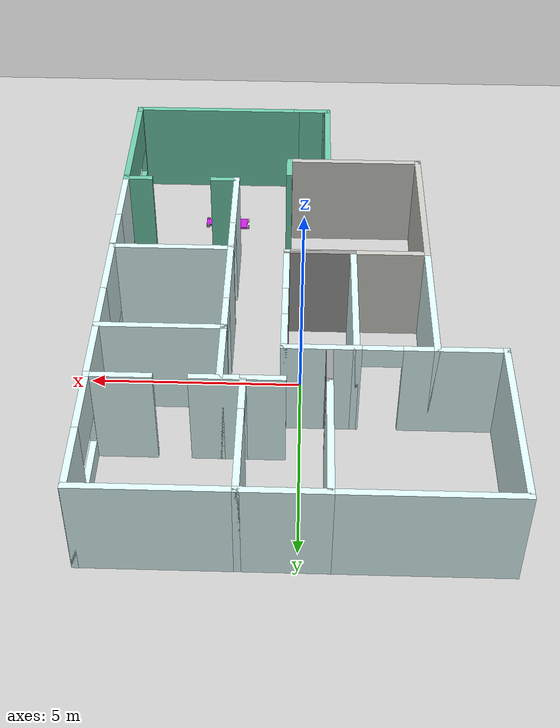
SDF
<sdf version="1.6">
 <world name="default">
  <plugin name="hello" filename="libhello_apartment.so"/>
  <light name="sun" type="directional">
   <pose>0 0 10 0 -0 0</pose>
   <diffuse>0.8 0.8 0.8 1</diffuse>
   <specular>0.2 0.2 0.2 1</specular>
   <attenuation>
    <range>1000</range>
    <constant>0.9</constant>
    <linear>0.01</linear>
    <quadratic>0.001</quadratic>
   </attenuation>
   <direction>-0.5 0.1 -0.9</direction>
  </light>
  <model name="ground_plane">
   <static>1</static>
   <link name="link">
    <collision name="collision">
     <geometry><plane><normal>0 0 1</normal><size>100 100</size></plane></geometry>
     <surface><friction><ode><mu>100</mu><mu2>50</mu2></ode></friction></surface>
    </collision>
    <visual name="visual">
     <cast_shadows>0</cast_shadows>
     <geometry><plane><normal>0 0 1</normal><size>100 100</size></plane></geometry>
     <material>
      <script><uri>file://media/materials/scripts/gazebo.material</uri><name>Gazebo/Grey</name></script>
     </material>
    </visual>
   </link>
  </model>
  <gravity>0 0 -9.8</gravity>
  <magnetic_field>6e-06 2.3e-05 -4.2e-05</magnetic_field>
  <atmosphere type="adiabatic"/>
  <physics name="default_physics" default="0" type="ode">
   <max_step_size>0.001</max_step_size>
   <real_time_factor>1</real_time_factor>
   <real_time_update_rate>1000</real_time_update_rate>
  </physics>
  <scene><ambient>0.4 0.4 0.4 1</ambient><background>0.7 0.7 0.7 1</background><shadows>1</shadows></scene>
  <spherical_coordinates>
   <surface_model>EARTH_WGS84</surface_model>
   <latitude_deg>0</latitude_deg>
   <longitude_deg>0</longitude_deg>
   <elevation>0</elevation>
   <heading_deg>0</heading_deg>
  </spherical_coordinates>
  <model name="Building">
   <pose>0.06239 -1.44031 0 0 -0 0</pose>
   <link name="Wall_1">
    <collision name="Wall_1_Collision">
     <geometry><box><size>3.5 0.15 2.5</size></box></geometry>
     <pose>0 0 1.25 0 -0 0</pose>
    </collision>
    <visual name="Wall_1_Visual">
     <pose>0 0 1.25 0 -0 0</pose>
     <geometry><box><size>3.5 0.15 2.5</size></box></geometry>
     <material>
      <script><uri>file://media/materials/scripts/gazebo.material</uri><name>Gazebo/Grey</name></script>
      <ambient>0.878431 1 0.996078 1</ambient>
     </material>
     <meta><layer>0</layer></meta>
    </visual>
    <pose>2.85 6.875 0 0 -0 0</pose>
   </link>
   <link name="Wall_10">
    <pose>-2.1 2.775 0 0 -0 0</pose>
    <visual name="Wall_10_Visual_0">
     <pose>-1.3425 0 1.25 0 -0 0</pose>
     <geometry><box><size>2.315 0.15 2.5</size></box></geometry>
     <material>
      <script><uri>file://media/materials/scripts/gazebo.material</uri><name>Gazebo/Grey</name></script>
      <ambient>0.878431 1 0.996078 1</ambient>
     </material>
     <meta><layer>0</layer></meta>
    </visual>
    <collision name="Wall_10_Collision_0">
     <geometry><box><size>2.315 0.15 2.5</size></box></geometry>
     <pose>-1.3425 0 1.25 0 -0 0</pose>
    </collision>
    <visual name="Wall_10_Visual_1">
     <pose>1.6075 0 1.25 0 -0 0</pose>
     <geometry><box><size>1.785 0.15 2.5</size></box></geometry>
     <material>
      <script><uri>file://media/materials/scripts/gazebo.material</uri><name>Gazebo/Grey</name></script>
      <ambient>0.878431 1 0.996078 1</ambient>
     </material>
     <meta><layer>0</layer></meta>
    </visual>
    <collision name="Wall_10_Collision_1">
     <geometry><box><size>1.785 0.15 2.5</size></box></geometry>
     <pose>1.6075 0 1.25 0 -0 0</pose>
    </collision>
    <visual name="Wall_10_Visual_2">
     <pose>0.265 0 2.25 0 -0 0</pose>
     <geometry><box><size>0.9 0.15 0.5</size></box></geometry>
     <material>
      <script><uri>file://media/materials/scripts/gazebo.material</uri><name>Gazebo/Grey</name></script>
      <ambient>0.878431 1 0.996078 1</ambient>
     </material>
     <meta><layer>0</layer></meta>
    </visual>
    <collision name="Wall_10_Collision_2">
     <geometry><box><size>0.9 0.15 0.5</size></box></geometry>
     <pose>0.265 0 2.25 0 -0 0</pose>
    </collision>
   </link>
   <link name="Wall_12">
    <collision name="Wall_12_Collision">
     <geometry><box><size>1.75 0.15 2.5</size></box></geometry>
     <pose>0 0 1.25 0 -0 0</pose>
    </collision>
    <visual name="Wall_12_Visual">
     <pose>0 0 1.25 0 -0 0</pose>
     <geometry><box><size>1.75 0.15 2.5</size></box></geometry>
     <material>
      <script><uri>file://media/materials/scripts/gazebo.material</uri><name>Gazebo/Grey</name></script>
      <ambient>0.878431 1 0.996078 1</ambient>
     </material>
     <meta><layer>0</layer></meta>
    </visual>
    <pose>4.525 2.975 0 0 0 -1.5708</pose>
   </link>
   <link name="Wall_16">
    <collision name="Wall_16_Collision">
     <geometry><box><size>3 0.15 2.5</size></box></geometry>
     <pose>0 0 1.25 0 -0 0</pose>
    </collision>
    <visual name="Wall_16_Visual">
     <pose>0 0 1.25 0 -0 0</pose>
     <geometry><box><size>3 0.15 2.5</size></box></geometry>
     <material>
      <script><uri>file://media/materials/scripts/gazebo.material</uri><name>Gazebo/Grey</name></script>
      <ambient>0.878431 1 0.996078 1</ambient>
     </material>
     <meta><layer>0</layer></meta>
    </visual>
    <pose>3.1 2.175 0 0 -0 3.14159</pose>
   </link>
   <link name="Wall_17">
    <collision name="Wall_17_Collision">
     <geometry><box><size>1.75 0.15 2.5</size></box></geometry>
     <pose>0 0 1.25 0 -0 0</pose>
    </collision>
    <visual name="Wall_17_Visual">
     <pose>0 0 1.25 0 -0 0</pose>
     <geometry><box><size>1.75 0.15 2.5</size></box></geometry>
     <material>
      <script><uri>file://media/materials/scripts/gazebo.material</uri><name>Gazebo/Grey</name></script>
      <ambient>0.878431 1 0.996078 1</ambient>
     </material>
     <meta><layer>0</layer></meta>
    </visual>
    <pose>1.675 2.975 0 0 -0 1.5708</pose>
   </link>
   <link name="Wall_19">
    <pose>4.525 0.75 0 0 0 -1.5708</pose>
    <visual name="Wall_19_Visual_0">
     <pose>-1.4225 0 1.25 0 -0 0</pose>
     <geometry><box><size>0.155 0.15 2.5</size></box></geometry>
     <material>
      <script><uri>file://media/materials/scripts/gazebo.material</uri><name>Gazebo/Grey</name></script>
      <ambient>0.878431 1 0.996078 1</ambient>
     </material>
     <meta><layer>0</layer></meta>
    </visual>
    <collision name="Wall_19_Collision_0">
     <geometry><box><size>0.155 0.15 2.5</size></box></geometry>
     <pose>-1.4225 0 1.25 0 -0 0</pose>
    </collision>
    <visual name="Wall_19_Visual_1">
     <pose>0.0775 0 0.25 0 -0 0</pose>
     <geometry><box><size>2.845 0.15 0.5</size></box></geometry>
     <material>
      <script><uri>file://media/materials/scripts/gazebo.material</uri><name>Gazebo/Grey</name></script>
      <ambient>0.878431 1 0.996078 1</ambient>
     </material>
     <meta><layer>0</layer></meta>
    </visual>
    <collision name="Wall_19_Collision_1">
     <geometry><box><size>2.845 0.15 0.5</size></box></geometry>
     <pose>0.0775 0 0.25 0 -0 0</pose>
    </collision>
    <visual name="Wall_19_Visual_2">
     <pose>0.6625 0 1.5 0 -0 0</pose>
     <geometry><box><size>1.675 0.15 2</size></box></geometry>
     <material>
      <script><uri>file://media/materials/scripts/gazebo.material</uri><name>Gazebo/Grey</name></script>
      <ambient>0.878431 1 0.996078 1</ambient>
     </material>
     <meta><layer>0</layer></meta>
    </visual>
    <collision name="Wall_19_Collision_2">
     <geometry><box><size>1.675 0.15 2</size></box></geometry>
     <pose>0.6625 0 1.5 0 -0 0</pose>
    </collision>
    <visual name="Wall_19_Visual_3">
     <pose>-0.76 0 1.9 0 -0 0</pose>
     <geometry><box><size>1.17 0.15 1.2</size></box></geometry>
     <material>
      <script><uri>file://media/materials/scripts/gazebo.material</uri><name>Gazebo/Grey</name></script>
      <ambient>0.878431 1 0.996078 1</ambient>
     </material>
     <meta><layer>0</layer></meta>
    </visual>
    <collision name="Wall_19_Collision_3">
     <geometry><box><size>1.17 0.15 1.2</size></box></geometry>
     <pose>-0.76 0 1.9 0 -0 0</pose>
    </collision>
   </link>
   <link name="Wall_2">
    <pose>4.525 5.325 0 0 0 -1.5708</pose>
    <visual name="Wall_2_Visual_0">
     <pose>-0.8175 0 1.25 0 -0 0</pose>
     <geometry><box><size>1.615 0.15 2.5</size></box></geometry>
     <material>
      <script><uri>file://media/materials/scripts/gazebo.material</uri><name>Gazebo/Grey</name></script>
      <ambient>0.878431 1 0.996078 1</ambient>
     </material>
     <meta><layer>0</layer></meta>
    </visual>
    <collision name="Wall_2_Collision_0">
     <geometry><box><size>1.615 0.15 2.5</size></box></geometry>
     <pose>-0.8175 0 1.25 0 -0 0</pose>
    </collision>
    <visual name="Wall_2_Visual_1">
     <pose>0.8075 0 0.25 0 -0 0</pose>
     <geometry><box><size>1.635 0.15 0.5</size></box></geometry>
     <material>
      <script><uri>file://media/materials/scripts/gazebo.material</uri><name>Gazebo/Grey</name></script>
      <ambient>0.878431 1 0.996078 1</ambient>
     </material>
     <meta><layer>0</layer></meta>
    </visual>
    <collision name="Wall_2_Collision_1">
     <geometry><box><size>1.635 0.15 0.5</size></box></geometry>
     <pose>0.8075 0 0.25 0 -0 0</pose>
    </collision>
    <visual name="Wall_2_Visual_2">
     <pose>1.5475 0 1.5 0 -0 0</pose>
     <geometry><box><size>0.155 0.15 2</size></box></geometry>
     <material>
      <script><uri>file://media/materials/scripts/gazebo.material</uri><name>Gazebo/Grey</name></script>
      <ambient>0.878431 1 0.996078 1</ambient>
     </material>
     <meta><layer>0</layer></meta>
    </visual>
    <collision name="Wall_2_Collision_2">
     <geometry><box><size>0.155 0.15 2</size></box></geometry>
     <pose>1.5475 0 1.5 0 -0 0</pose>
    </collision>
    <visual name="Wall_2_Visual_3">
     <pose>0.73 0 1.9 0 -0 0</pose>
     <geometry><box><size>1.48 0.15 1.2</size></box></geometry>
     <material>
      <script><uri>file://media/materials/scripts/gazebo.material</uri><name>Gazebo/Grey</name></script>
      <ambient>0.878431 1 0.996078 1</ambient>
     </material>
     <meta><layer>0</layer></meta>
    </visual>
    <collision name="Wall_2_Collision_3">
     <geometry><box><size>1.48 0.15 1.2</size></box></geometry>
     <pose>0.73 0 1.9 0 -0 0</pose>
    </collision>
   </link>
   <link name="Wall_20">
    <collision name="Wall_20_Collision">
     <geometry><box><size>3 0.15 2.5</size></box></geometry>
     <pose>0 0 1.25 0 -0 0</pose>
    </collision>
    <visual name="Wall_20_Visual">
     <pose>0 0 1.25 0 -0 0</pose>
     <geometry><box><size>3 0.15 2.5</size></box></geometry>
     <material>
      <script><uri>file://media/materials/scripts/gazebo.material</uri><name>Gazebo/Grey</name></script>
      <ambient>0.878431 1 0.996078 1</ambient>
     </material>
     <meta><layer>0</layer></meta>
    </visual>
    <pose>3.1 -0.675 0 0 -0 3.14159</pose>
   </link>
   <link name="Wall_21">
    <pose>1.675 0.75 0 0 -0 1.5708</pose>
    <visual name="Wall_21_Visual_0">
     <pose>-0.5275 0 1.25 0 -0 0</pose>
     <geometry><box><size>1.945 0.15 2.5</size></box></geometry>
     <material>
      <script><uri>file://media/materials/scripts/gazebo.material</uri><name>Gazebo/Grey</name></script>
      <ambient>0.878431 1 0.996078 1</ambient>
     </material>
     <meta><layer>0</layer></meta>
    </visual>
    <collision name="Wall_21_Collision_0">
     <geometry><box><size>1.945 0.15 2.5</size></box></geometry>
     <pose>-0.5275 0 1.25 0 -0 0</pose>
    </collision>
    <visual name="Wall_21_Visual_1">
     <pose>1.4225 0 1.25 0 -0 0</pose>
     <geometry><box><size>0.155 0.15 2.5</size></box></geometry>
     <material>
      <script><uri>file://media/materials/scripts/gazebo.material</uri><name>Gazebo/Grey</name></script>
      <ambient>0.878431 1 0.996078 1</ambient>
     </material>
     <meta><layer>0</layer></meta>
    </visual>
    <collision name="Wall_21_Collision_1">
     <geometry><box><size>0.155 0.15 2.5</size></box></geometry>
     <pose>1.4225 0 1.25 0 -0 0</pose>
    </collision>
    <visual name="Wall_21_Visual_2">
     <pose>0.895 0 2.25 0 -0 0</pose>
     <geometry><box><size>0.9 0.15 0.5</size></box></geometry>
     <material>
      <script><uri>file://media/materials/scripts/gazebo.material</uri><name>Gazebo/Grey</name></script>
      <ambient>0.878431 1 0.996078 1</ambient>
     </material>
     <meta><layer>0</layer></meta>
    </visual>
    <collision name="Wall_21_Collision_2">
     <geometry><box><size>0.9 0.15 0.5</size></box></geometry>
     <pose>0.895 0 2.25 0 -0 0</pose>
    </collision>
   </link>
   <link name="Wall_23">
    <pose>0.325 1.1 0 0 0 -1.5708</pose>
    <visual name="Wall_23_Visual_0">
     <pose>-1.1775 0 1.25 0 -0 0</pose>
     <geometry><box><size>1.145 0.15 2.5</size></box></geometry>
     <material>
      <script><uri>file://media/materials/scripts/gazebo.material</uri><name>Gazebo/Grey</name></script>
      <ambient>0.878431 1 0.996078 1</ambient>
     </material>
     <meta><layer>0</layer></meta>
    </visual>
    <collision name="Wall_23_Collision_0">
     <geometry><box><size>1.145 0.15 2.5</size></box></geometry>
     <pose>-1.1775 0 1.25 0 -0 0</pose>
    </collision>
    <visual name="Wall_23_Visual_1">
     <pose>1.0225 0 1.25 0 -0 0</pose>
     <geometry><box><size>1.455 0.15 2.5</size></box></geometry>
     <material>
      <script><uri>file://media/materials/scripts/gazebo.material</uri><name>Gazebo/Grey</name></script>
      <ambient>0.878431 1 0.996078 1</ambient>
     </material>
     <meta><layer>0</layer></meta>
    </visual>
    <collision name="Wall_23_Collision_1">
     <geometry><box><size>1.455 0.15 2.5</size></box></geometry>
     <pose>1.0225 0 1.25 0 -0 0</pose>
    </collision>
    <visual name="Wall_23_Visual_2">
     <pose>-0.155 0 2.25 0 -0 0</pose>
     <geometry><box><size>0.9 0.15 0.5</size></box></geometry>
     <material>
      <script><uri>file://media/materials/scripts/gazebo.material</uri><name>Gazebo/Grey</name></script>
      <ambient>0.878431 1 0.996078 1</ambient>
     </material>
     <meta><layer>0</layer></meta>
    </visual>
    <collision name="Wall_23_Collision_2">
     <geometry><box><size>0.9 0.15 0.5</size></box></geometry>
     <pose>-0.155 0 2.25 0 -0 0</pose>
    </collision>
   </link>
   <link name="Wall_25">
    <pose>4.525 -2.1 0 0 0 -1.5708</pose>
    <visual name="Wall_25_Visual_0">
     <pose>-1.4225 0 1.25 0 -0 0</pose>
     <geometry><box><size>0.155 0.15 2.5</size></box></geometry>
     <material>
      <script><uri>file://media/materials/scripts/gazebo.material</uri><name>Gazebo/Grey</name></script>
      <ambient>0.878431 1 0.996078 1</ambient>
     </material>
     <meta><layer>0</layer></meta>
    </visual>
    <collision name="Wall_25_Collision_0">
     <geometry><box><size>0.155 0.15 2.5</size></box></geometry>
     <pose>-1.4225 0 1.25 0 -0 0</pose>
    </collision>
    <visual name="Wall_25_Visual_1">
     <pose>0.0775 0 0.25 0 -0 0</pose>
     <geometry><box><size>2.845 0.15 0.5</size></box></geometry>
     <material>
      <script><uri>file://media/materials/scripts/gazebo.material</uri><name>Gazebo/Grey</name></script>
      <ambient>0.878431 1 0.996078 1</ambient>
     </material>
     <meta><layer>0</layer></meta>
    </visual>
    <collision name="Wall_25_Collision_1">
     <geometry><box><size>2.845 0.15 0.5</size></box></geometry>
     <pose>0.0775 0 0.25 0 -0 0</pose>
    </collision>
    <visual name="Wall_25_Visual_2">
     <pose>0.6625 0 1.5 0 -0 0</pose>
     <geometry><box><size>1.675 0.15 2</size></box></geometry>
     <material>
      <script><uri>file://media/materials/scripts/gazebo.material</uri><name>Gazebo/Grey</name></script>
      <ambient>0.878431 1 0.996078 1</ambient>
     </material>
     <meta><layer>0</layer></meta>
    </visual>
    <collision name="Wall_25_Collision_2">
     <geometry><box><size>1.675 0.15 2</size></box></geometry>
     <pose>0.6625 0 1.5 0 -0 0</pose>
    </collision>
    <visual name="Wall_25_Visual_3">
     <pose>-0.76 0 1.9 0 -0 0</pose>
     <geometry><box><size>1.17 0.15 1.2</size></box></geometry>
     <material>
      <script><uri>file://media/materials/scripts/gazebo.material</uri><name>Gazebo/Grey</name></script>
      <ambient>0.878431 1 0.996078 1</ambient>
     </material>
     <meta><layer>0</layer></meta>
    </visual>
    <collision name="Wall_25_Collision_3">
     <geometry><box><size>1.17 0.15 1.2</size></box></geometry>
     <pose>-0.76 0 1.9 0 -0 0</pose>
    </collision>
   </link>
   <link name="Wall_26">
    <collision name="Wall_26_Collision">
     <geometry><box><size>0.75 0.15 2.5</size></box></geometry>
     <pose>0 0 1.25 0 -0 0</pose>
    </collision>
    <visual name="Wall_26_Visual">
     <pose>0 0 1.25 0 -0 0</pose>
     <geometry><box><size>0.75 0.15 2.5</size></box></geometry>
     <material>
      <script><uri>file://media/materials/scripts/gazebo.material</uri><name>Gazebo/Grey</name></script>
      <ambient>0.435294 0.796078 0.67451 1</ambient>
     </material>
     <meta><layer>0</layer></meta>
    </visual>
    <pose>4.225 -3.525 0 0 -0 3.14159</pose>
   </link>
   <link name="Wall_28">
    <pose>1.675 -2.1 0 0 0 -1.5708</pose>
    <visual name="Wall_28_Visual_0">
     <pose>-1.4225 0 1.25 0 -0 0</pose>
     <geometry><box><size>0.155 0.15 2.5</size></box></geometry>
     <material>
      <script><uri>file://media/materials/scripts/gazebo.material</uri><name>Gazebo/Grey</name></script>
      <ambient>0.878431 1 0.996078 1</ambient>
     </material>
     <meta><layer>0</layer></meta>
    </visual>
    <collision name="Wall_28_Collision_0">
     <geometry><box><size>0.155 0.15 2.5</size></box></geometry>
     <pose>-1.4225 0 1.25 0 -0 0</pose>
    </collision>
    <visual name="Wall_28_Visual_1">
     <pose>0.5275 0 1.25 0 -0 0</pose>
     <geometry><box><size>1.945 0.15 2.5</size></box></geometry>
     <material>
      <script><uri>file://media/materials/scripts/gazebo.material</uri><name>Gazebo/Grey</name></script>
      <ambient>0.878431 1 0.996078 1</ambient>
     </material>
     <meta><layer>0</layer></meta>
    </visual>
    <collision name="Wall_28_Collision_1">
     <geometry><box><size>1.945 0.15 2.5</size></box></geometry>
     <pose>0.5275 0 1.25 0 -0 0</pose>
    </collision>
    <visual name="Wall_28_Visual_2">
     <pose>-0.895 0 2.25 0 -0 0</pose>
     <geometry><box><size>0.9 0.15 0.5</size></box></geometry>
     <material>
      <script><uri>file://media/materials/scripts/gazebo.material</uri><name>Gazebo/Grey</name></script>
      <ambient>0.878431 1 0.996078 1</ambient>
     </material>
     <meta><layer>0</layer></meta>
    </visual>
    <collision name="Wall_28_Collision_2">
     <geometry><box><size>0.9 0.15 0.5</size></box></geometry>
     <pose>-0.895 0 2.25 0 -0 0</pose>
    </collision>
   </link>
   <link name="Wall_29">
    <collision name="Wall_29_Collision">
     <geometry><box><size>0.75 0.15 2.5</size></box></geometry>
     <pose>0 0 1.25 0 -0 0</pose>
    </collision>
    <visual name="Wall_29_Visual">
     <pose>0 0 1.25 0 -0 0</pose>
     <geometry><box><size>0.75 0.15 2.5</size></box></geometry>
     <material>
      <script><uri>file://media/materials/scripts/gazebo.material</uri><name>Gazebo/Grey</name></script>
      <ambient>0.435294 0.796078 0.67451 1</ambient>
     </material>
     <meta><layer>0</layer></meta>
    </visual>
    <pose>1.975 -3.525 0 0 -0 0</pose>
   </link>
   <link name="Wall_31">
    <collision name="Wall_31_Collision">
     <geometry><box><size>1.73 0.15 2.5</size></box></geometry>
     <pose>0 0 1.25 0 -0 0</pose>
    </collision>
    <visual name="Wall_31_Visual">
     <pose>0 0 1.25 0 -0 0</pose>
     <geometry><box><size>1.73 0.15 2.5</size></box></geometry>
     <material>
      <script><uri>file://media/materials/scripts/gazebo.material</uri><name>Gazebo/Grey</name></script>
      <ambient>1 1 1 1</ambient>
     </material>
     <meta><layer>0</layer></meta>
    </visual>
    <pose>-0.465 -0.575 0 0 -0 3.14159</pose>
   </link>
   <link name="Wall_32">
    <collision name="Wall_32_Collision">
     <geometry><box><size>3.5 0.15 2.5</size></box></geometry>
     <pose>0 0 1.25 0 -0 0</pose>
    </collision>
    <visual name="Wall_32_Visual">
     <pose>0 0 1.25 0 -0 0</pose>
     <geometry><box><size>3.5 0.15 2.5</size></box></geometry>
     <material>
      <script><uri>file://media/materials/scripts/gazebo.material</uri><name>Gazebo/Grey</name></script>
      <ambient>0.878431 1 0.996078 1</ambient>
     </material>
     <meta><layer>0</layer></meta>
    </visual>
    <pose>-1.265 1.1 0 0 -0 1.5708</pose>
   </link>
   <link name="Wall_34">
    <collision name="Wall_34_Collision">
     <geometry><box><size>3.5 0.15 2.5</size></box></geometry>
     <pose>0 0 1.25 0 -0 0</pose>
    </collision>
    <visual name="Wall_34_Visual">
     <pose>0 0 1.25 0 -0 0</pose>
     <geometry><box><size>3.5 0.15 2.5</size></box></geometry>
     <material>
      <script><uri>file://media/materials/scripts/gazebo.material</uri><name>Gazebo/CeilingTiled</name></script>
      <ambient>0.435294 0.796078 0.67451 1</ambient>
     </material>
     <meta><layer>0</layer></meta>
    </visual>
    <pose>-1.35 -0.575 0 0 -0 3.14159</pose>
   </link>
   <link name="Wall_36">
    <collision name="Wall_36_Collision">
     <geometry><box><size>4 0.15 2.5</size></box></geometry>
     <pose>0 0 1.25 0 -0 0</pose>
    </collision>
    <visual name="Wall_36_Visual">
     <pose>0 0 1.25 0 -0 0</pose>
     <geometry><box><size>4 0.15 2.5</size></box></geometry>
     <material>
      <script><uri>file://media/materials/scripts/gazebo.material</uri><name>Gazebo/CeilingTiled</name></script>
      <ambient>0.435294 0.796078 0.67451 1</ambient>
     </material>
     <meta><layer>0</layer></meta>
    </visual>
    <pose>-3.025 -2.5 0 0 0 -1.5708</pose>
   </link>
   <link name="Wall_37">
    <collision name="Wall_37_Collision">
     <geometry><box><size>3.5 0.15 2.5</size></box></geometry>
     <pose>0 0 1.25 0 -0 0</pose>
    </collision>
    <visual name="Wall_37_Visual">
     <pose>0 0 1.25 0 -0 0</pose>
     <geometry><box><size>3.5 0.15 2.5</size></box></geometry>
     <material>
      <script><uri>file://media/materials/scripts/gazebo.material</uri><name>Gazebo/CeilingTiled</name></script>
      <ambient>0.435294 0.796078 0.67451 1</ambient>
     </material>
     <meta><layer>0</layer></meta>
    </visual>
    <pose>-1.35 -4.425 0 0 -0 0</pose>
   </link>
   <link name="Wall_38">
    <collision name="Wall_38_Collision">
     <geometry><box><size>0.75 0.15 2.5</size></box></geometry>
     <pose>0 0 1.25 0 -0 0</pose>
    </collision>
    <visual name="Wall_38_Visual">
     <pose>0 0 1.25 0 -0 0</pose>
     <geometry><box><size>0.75 0.15 2.5</size></box></geometry>
     <material>
      <script><uri>file://media/materials/scripts/gazebo.material</uri><name>Gazebo/Grey</name></script>
      <ambient>0.435294 0.796078 0.67451 1</ambient>
     </material>
     <meta><layer>0</layer></meta>
    </visual>
    <pose>0.325 -4.125 0 0 -0 1.5708</pose>
   </link>
   <link name="Wall_4">
    <pose>1.175 5.325 0 0 -0 1.5708</pose>
    <visual name="Wall_4_Visual_0">
     <pose>-1.5775 0 1.25 0 -0 0</pose>
     <geometry><box><size>0.095 0.15 2.5</size></box></geometry>
     <material>
      <script><uri>file://media/materials/scripts/gazebo.material</uri><name>Gazebo/Grey</name></script>
      <ambient>0.878431 1 0.996078 1</ambient>
     </material>
     <meta><layer>0</layer></meta>
    </visual>
    <collision name="Wall_4_Collision_0">
     <geometry><box><size>0.095 0.15 2.5</size></box></geometry>
     <pose>-1.5775 0 1.25 0 -0 0</pose>
    </collision>
    <visual name="Wall_4_Visual_1">
     <pose>0.4975 0 1.25 0 -0 0</pose>
     <geometry><box><size>2.255 0.15 2.5</size></box></geometry>
     <material>
      <script><uri>file://media/materials/scripts/gazebo.material</uri><name>Gazebo/Grey</name></script>
      <ambient>0.878431 1 0.996078 1</ambient>
     </material>
     <meta><layer>0</layer></meta>
    </visual>
    <collision name="Wall_4_Collision_1">
     <geometry><box><size>2.255 0.15 2.5</size></box></geometry>
     <pose>0.4975 0 1.25 0 -0 0</pose>
    </collision>
    <visual name="Wall_4_Visual_2">
     <pose>-1.08 0 2.25 0 -0 0</pose>
     <geometry><box><size>0.9 0.15 0.5</size></box></geometry>
     <material>
      <script><uri>file://media/materials/scripts/gazebo.material</uri><name>Gazebo/Grey</name></script>
      <ambient>0.878431 1 0.996078 1</ambient>
     </material>
     <meta><layer>0</layer></meta>
    </visual>
    <collision name="Wall_4_Collision_2">
     <geometry><box><size>0.9 0.15 0.5</size></box></geometry>
     <pose>-1.08 0 2.25 0 -0 0</pose>
    </collision>
   </link>
   <link name="Wall_42">
    <pose>4.525 -5.2 0 0 0 -1.5708</pose>
    <visual name="Wall_42_Visual_0">
     <pose>-1.6525 0 1.25 0 -0 0</pose>
     <geometry><box><size>0.195 0.15 2.5</size></box></geometry>
     <material>
      <script><uri>file://media/materials/scripts/gazebo.material</uri><name>Gazebo/Grey</name></script>
      <ambient>0.435294 0.796078 0.67451 1</ambient>
     </material>
     <meta><layer>0</layer></meta>
    </visual>
    <collision name="Wall_42_Collision_0">
     <geometry><box><size>0.195 0.15 2.5</size></box></geometry>
     <pose>-1.6525 0 1.25 0 -0 0</pose>
    </collision>
    <visual name="Wall_42_Visual_1">
     <pose>0.0975 0 0.25 0 -0 0</pose>
     <geometry><box><size>3.305 0.15 0.5</size></box></geometry>
     <material>
      <script><uri>file://media/materials/scripts/gazebo.material</uri><name>Gazebo/Grey</name></script>
      <ambient>0.435294 0.796078 0.67451 1</ambient>
     </material>
     <meta><layer>0</layer></meta>
    </visual>
    <collision name="Wall_42_Collision_1">
     <geometry><box><size>3.305 0.15 0.5</size></box></geometry>
     <pose>0.0975 0 0.25 0 -0 0</pose>
    </collision>
    <visual name="Wall_42_Visual_2">
     <pose>1.6325 0 1.5 0 -0 0</pose>
     <geometry><box><size>0.235 0.15 2</size></box></geometry>
     <material>
      <script><uri>file://media/materials/scripts/gazebo.material</uri><name>Gazebo/Grey</name></script>
      <ambient>0.435294 0.796078 0.67451 1</ambient>
     </material>
     <meta><layer>0</layer></meta>
    </visual>
    <collision name="Wall_42_Collision_2">
     <geometry><box><size>0.235 0.15 2</size></box></geometry>
     <pose>1.6325 0 1.5 0 -0 0</pose>
    </collision>
    <visual name="Wall_42_Visual_3">
     <pose>-0.02 0 1.9 0 -0 0</pose>
     <geometry><box><size>3.07 0.15 1.2</size></box></geometry>
     <material>
      <script><uri>file://media/materials/scripts/gazebo.material</uri><name>Gazebo/Grey</name></script>
      <ambient>0.435294 0.796078 0.67451 1</ambient>
     </material>
     <meta><layer>0</layer></meta>
    </visual>
    <collision name="Wall_42_Collision_3">
     <geometry><box><size>3.07 0.15 1.2</size></box></geometry>
     <pose>-0.02 0 1.9 0 -0 0</pose>
    </collision>
   </link>
   <link name="Wall_43">
    <collision name="Wall_43_Collision">
     <geometry><box><size>4.5 0.15 2.5</size></box></geometry>
     <pose>0 0 1.25 0 -0 0</pose>
    </collision>
    <visual name="Wall_43_Visual">
     <pose>0 0 1.25 0 -0 0</pose>
     <geometry><box><size>4.5 0.15 2.5</size></box></geometry>
     <material>
      <script><uri>file://media/materials/scripts/gazebo.material</uri><name>Gazebo/Grey</name></script>
      <ambient>0.435294 0.796078 0.67451 1</ambient>
     </material>
     <meta><layer>0</layer></meta>
    </visual>
    <pose>2.35 -6.875 0 0 -0 3.14159</pose>
   </link>
   <link name="Wall_45">
    <pose>-0.25 -6.875 0 0 -0 3.14159</pose>
    <visual name="Wall_45_Visual_0">
     <pose>0 0 1.25 0 -0 0</pose>
     <geometry><box><size>1 0.15 2.5</size></box></geometry>
     <material>
      <script><uri>file://media/materials/scripts/gazebo.material</uri><name>Gazebo/Grey</name></script>
      <ambient>0.435294 0.796078 0.67451 1</ambient>
     </material>
     <meta><layer>0</layer></meta>
    </visual>
    <collision name="Wall_45_Collision_0">
     <geometry><box><size>1 0.15 2.5</size></box></geometry>
     <pose>0 0 1.25 0 -0 0</pose>
    </collision>
    <visual name="Wall_45_Visual_1">
     <pose>0.4025 0 1.25 0 -0 0</pose>
     <geometry><box><size>0.195 0.15 2.5</size></box></geometry>
     <material>
      <script><uri>file://media/materials/scripts/gazebo.material</uri><name>Gazebo/Grey</name></script>
      <ambient>0.435294 0.796078 0.67451 1</ambient>
     </material>
     <meta><layer>0</layer></meta>
    </visual>
    <collision name="Wall_45_Collision_1">
     <geometry><box><size>0.195 0.15 2.5</size></box></geometry>
     <pose>0.4025 0 1.25 0 -0 0</pose>
    </collision>
   </link>
   <link name="Wall_46">
    <collision name="Wall_46_Collision">
     <geometry><box><size>2.5 0.15 2.5</size></box></geometry>
     <pose>0 0 1.25 0 -0 0</pose>
    </collision>
    <visual name="Wall_46_Visual">
     <pose>0 0 1.25 0 -0 0</pose>
     <geometry><box><size>2.5 0.15 2.5</size></box></geometry>
     <material>
      <script><uri>file://media/materials/scripts/gazebo.material</uri><name>Gazebo/Grey</name></script>
      <ambient>0.435294 0.796078 0.67451 1</ambient>
     </material>
     <meta><layer>0</layer></meta>
    </visual>
    <pose>-0.675 -5.7 0 0 -0 1.5708</pose>
   </link>
   <link name="Wall_48">
    <pose>-0.675 3.35 0 0 0 -1.5708</pose>
    <visual name="Wall_48_Visual_0">
     <pose>-0.4525 0 1.25 0 -0 0</pose>
     <geometry><box><size>0.095 0.15 2.5</size></box></geometry>
     <material>
      <script><uri>file://media/materials/scripts/gazebo.material</uri><name>Gazebo/Grey</name></script>
      <ambient>1 1 1 1</ambient>
     </material>
     <meta><layer>0</layer></meta>
    </visual>
    <collision name="Wall_48_Collision_0">
     <geometry><box><size>0.095 0.15 2.5</size></box></geometry>
     <pose>-0.4525 0 1.25 0 -0 0</pose>
    </collision>
    <visual name="Wall_48_Visual_1">
     <pose>0.4975 0 1.25 0 -0 0</pose>
     <geometry><box><size>0.005 0.15 2.5</size></box></geometry>
     <material>
      <script><uri>file://media/materials/scripts/gazebo.material</uri><name>Gazebo/Grey</name></script>
      <ambient>1 1 1 1</ambient>
     </material>
     <meta><layer>0</layer></meta>
    </visual>
    <collision name="Wall_48_Collision_1">
     <geometry><box><size>0.005 0.15 2.5</size></box></geometry>
     <pose>0.4975 0 1.25 0 -0 0</pose>
    </collision>
    <visual name="Wall_48_Visual_2">
     <pose>0.045 0 2.25 0 -0 0</pose>
     <geometry><box><size>0.9 0.15 0.5</size></box></geometry>
     <material>
      <script><uri>file://media/materials/scripts/gazebo.material</uri><name>Gazebo/Grey</name></script>
      <ambient>1 1 1 1</ambient>
     </material>
     <meta><layer>0</layer></meta>
    </visual>
    <collision name="Wall_48_Collision_2">
     <geometry><box><size>0.9 0.15 0.5</size></box></geometry>
     <pose>0.045 0 2.25 0 -0 0</pose>
    </collision>
   </link>
   <link name="Wall_5">
    <collision name="Wall_5_Collision">
     <geometry><box><size>2 0.15 2.5</size></box></geometry>
     <pose>0 0 1.25 0 -0 0</pose>
    </collision>
    <visual name="Wall_5_Visual">
     <pose>0 0 1.25 0 -0 0</pose>
     <geometry><box><size>2 0.15 2.5</size></box></geometry>
     <material>
      <script><uri>file://media/materials/scripts/gazebo.material</uri><name>Gazebo/Grey</name></script>
      <ambient>0.878431 1 0.996078 1</ambient>
     </material>
     <meta><layer>0</layer></meta>
    </visual>
    <pose>0.25 6.875 0 0 -0 3.14159</pose>
   </link>
   <link name="Wall_50">
    <collision name="Wall_50_Collision">
     <geometry><box><size>1 0.15 2.5</size></box></geometry>
     <pose>0 0 1.25 0 -0 0</pose>
    </collision>
    <visual name="Wall_50_Visual">
     <pose>0 0 1.25 0 -0 0</pose>
     <geometry><box><size>1 0.15 2.5</size></box></geometry>
     <material>
      <script><uri>file://media/materials/scripts/gazebo.material</uri><name>Gazebo/Grey</name></script>
      <ambient>0.878431 1 0.996078 1</ambient>
     </material>
     <meta><layer>0</layer></meta>
    </visual>
    <pose>0.75 3.775 0 0 -0 3.14159</pose>
   </link>
   <link name="Wall_52">
    <collision name="Wall_52_Collision">
     <geometry><box><size>3.5 0.15 2.5</size></box></geometry>
     <pose>0 0 1.25 0 -0 0</pose>
    </collision>
    <visual name="Wall_52_Visual">
     <pose>0 0 1.25 0 -0 0</pose>
     <geometry><box><size>3.5 0.15 2.5</size></box></geometry>
     <material>
      <script><uri>file://media/materials/scripts/gazebo.material</uri><name>Gazebo/Grey</name></script>
      <ambient>0.878431 1 0.996078 1</ambient>
     </material>
     <meta><layer>0</layer></meta>
    </visual>
    <pose>-3.025 1.1 0 0 -0 1.5708</pose>
   </link>
   <link name="Wall_54">
    <collision name="Wall_54_Collision">
     <geometry><box><size>1.25 0.15 2.5</size></box></geometry>
     <pose>0 0 1.25 0 -0 0</pose>
    </collision>
    <visual name="Wall_54_Visual">
     <pose>0 0 1.25 0 -0 0</pose>
     <geometry><box><size>1.25 0.15 2.5</size></box></geometry>
     <material>
      <script><uri>file://media/materials/scripts/gazebo.material</uri><name>Gazebo/Grey</name></script>
      <ambient>0.878431 1 0.996078 1</ambient>
     </material>
     <meta><layer>0</layer></meta>
    </visual>
    <pose>1.725 3.775 0 0 -0 0</pose>
   </link>
   <link name="Wall_56">
    <collision name="Wall_56_Collision">
     <geometry><box><size>1.5 0.15 2.5</size></box></geometry>
     <pose>0 0 1.25 0 -0 0</pose>
    </collision>
    <visual name="Wall_56_Visual">
     <pose>0 0 1.25 0 -0 0</pose>
     <geometry><box><size>1.5 0.15 2.5</size></box></geometry>
     <material>
      <script><uri>file://media/materials/scripts/gazebo.material</uri><name>Gazebo/Grey</name></script>
      <ambient>0.878431 1 0.996078 1</ambient>
     </material>
     <meta><layer>0</layer></meta>
    </visual>
    <pose>3.85 3.775 0 0 -0 3.14159</pose>
   </link>
   <link name="Wall_6">
    <collision name="Wall_6_Collision">
     <geometry><box><size>3.25 0.15 2.5</size></box></geometry>
     <pose>0 0 1.25 0 -0 0</pose>
    </collision>
    <visual name="Wall_6_Visual">
     <pose>0 0 1.25 0 -0 0</pose>
     <geometry><box><size>3.25 0.15 2.5</size></box></geometry>
     <material>
      <script><uri>file://media/materials/scripts/gazebo.material</uri><name>Gazebo/Grey</name></script>
      <ambient>0.878431 1 0.996078 1</ambient>
     </material>
     <meta><layer>0</layer></meta>
    </visual>
    <pose>-0.675 5.325 0 0 0 -1.5708</pose>
   </link>
   <link name="Wall_8">
    <collision name="Wall_8_Collision">
     <geometry><box><size>4 0.15 2.5</size></box></geometry>
     <pose>0 0 1.25 0 -0 0</pose>
    </collision>
    <visual name="Wall_8_Visual">
     <pose>0 0 1.25 0 -0 0</pose>
     <geometry><box><size>4 0.15 2.5</size></box></geometry>
     <material>
      <script><uri>file://media/materials/scripts/gazebo.material</uri><name>Gazebo/Grey</name></script>
      <ambient>0.878431 1 0.996078 1</ambient>
     </material>
     <meta><layer>0</layer></meta>
    </visual>
    <pose>-2.6 6.875 0 0 -0 3.14159</pose>
   </link>
   <link name="Wall_9">
    <collision name="Wall_9_Collision">
     <geometry><box><size>4.25 0.15 2.5</size></box></geometry>
     <pose>0 0 1.25 0 -0 0</pose>
    </collision>
    <visual name="Wall_9_Visual">
     <pose>0 0 1.25 0 -0 0</pose>
     <geometry><box><size>4.25 0.15 2.5</size></box></geometry>
     <material>
      <script><uri>file://media/materials/scripts/gazebo.material</uri><name>Gazebo/Grey</name></script>
      <ambient>0.878431 1 0.996078 1</ambient>
     </material>
     <meta><layer>0</layer></meta>
    </visual>
    <pose>-4.525 4.825 0 0 0 -1.5708</pose>
   </link>
   <static>1</static>
  </model>
  <model name="RobotCar_0">
   <link name="link_0">
    <inertial>
     <mass>1</mass>
     <inertia>
      <ixx>0.166667</ixx>
      <ixy>0</ixy>
      <ixz>0</ixz>
      <iyy>0.166667</iyy>
      <iyz>0</iyz>
      <izz>0.166667</izz>
     </inertia>
    </inertial>
    <pose>0.074066 0.027028 0 0 -0 0</pose>
    <visual name="visual">
     <geometry><box><size>0.25 0.4 0.05</size></box></geometry>
     <material>
      <lighting>1</lighting>
      <script><uri>file://media/materials/scripts/gazebo.material</uri><name>Gazebo/Grey</name></script>
      <shader type="pixel"><normal_map>__default__</normal_map></shader>
      <ambient>0.8 0.1 0.9 1</ambient>
      <diffuse>0.8 0.1 0.9 1</diffuse>
      <specular>0.01 0.01 0.01 1</specular>
      <emissive>0 0 0 1</emissive>
     </material>
    </visual>
    <collision name="collision">
     <geometry><box><size>0.25 0.4 0.05</size></box></geometry>
     <surface>
      <friction>
       <ode><mu>1</mu><mu2>1</mu2><fdir1>0 0 0</fdir1><slip1>0</slip1><slip2>0</slip2></ode>
       <torsional>
        <coefficient>1</coefficient>
        <patch_radius>0</patch_radius>
        <surface_radius>0</surface_radius>
        <use_patch_radius>1</use_patch_radius>
        <ode><slip>0</slip></ode>
       </torsional>
      </friction>
      <bounce><restitution_coefficient>0</restitution_coefficient><threshold>1e+06</threshold></bounce>
      <contact>
       <collide_without_contact>0</collide_without_contact>
       <collide_without_contact_bitmask>1</collide_without_contact_bitmask>
       <collide_bitmask>1</collide_bitmask>
       <ode>
        <soft_cfm>0</soft_cfm>
        <soft_erp>0.2</soft_erp>
        <kp>1e+13</kp>
        <kd>1</kd>
        <max_vel>0.01</max_vel>
        <min_depth>0</min_depth>
       </ode>
       <bullet>
        <split_impulse>1</split_impulse>
        <split_impulse_penetration_threshold>-0.01</split_impulse_penetration_threshold>
        <soft_cfm>0</soft_cfm>
        <soft_erp>0.2</soft_erp>
        <kp>1e+13</kp>
        <kd>1</kd>
       </bullet>
      </contact>
     </surface>
    </collision>
   </link>
   <link name="link_1_clone_0">
    <inertial>
     <mass>1</mass>
     <inertia><ixx>0.145833</ixx><ixy>0</ixy><ixz>0</ixz><iyy>0.145833</iyy><iyz>0</iyz><izz>0.125</izz></inertia>
    </inertial>
    <pose>-0.075934 0.177028 0 1.5707 0 1.5707</pose>
    <visual name="visual">
     <geometry><cylinder><radius>0.05</radius><length>0.05</length></cylinder></geometry>
     <material>
      <lighting>1</lighting>
      <script><uri>file://media/materials/scripts/gazebo.material</uri><name>Gazebo/Grey</name></script>
      <shader type="pixel"><normal_map>__default__</normal_map></shader>
      <ambient>0.3 0.3 0.3 1</ambient>
      <diffuse>0.7 0.7 0.7 1</diffuse>
      <specular>0.01 0.01 0.01 1</specular>
      <emissive>0 0 0 1</emissive>
     </material>
    </visual>
    <collision name="collision">
     <geometry><cylinder><radius>0.05</radius><length>0.05</length></cylinder></geometry>
     <surface>
      <friction>
       <ode><mu>1</mu><mu2>1</mu2><fdir1>0 0 0</fdir1><slip1>0</slip1><slip2>0</slip2></ode>
       <torsional>
        <coefficient>1</coefficient>
        <patch_radius>0</patch_radius>
        <surface_radius>0</surface_radius>
        <use_patch_radius>1</use_patch_radius>
        <ode><slip>0</slip></ode>
       </torsional>
      </friction>
      <bounce><restitution_coefficient>0</restitution_coefficient><threshold>1e+06</threshold></bounce>
      <contact>
       <collide_without_contact>0</collide_without_contact>
       <collide_without_contact_bitmask>1</collide_without_contact_bitmask>
       <collide_bitmask>1</collide_bitmask>
       <ode>
        <soft_cfm>0</soft_cfm>
        <soft_erp>0.2</soft_erp>
        <kp>1e+13</kp>
        <kd>1</kd>
        <max_vel>0.01</max_vel>
        <min_depth>0</min_depth>
       </ode>
       <bullet>
        <split_impulse>1</split_impulse>
        <split_impulse_penetration_threshold>-0.01</split_impulse_penetration_threshold>
        <soft_cfm>0</soft_cfm>
        <soft_erp>0.2</soft_erp>
        <kp>1e+13</kp>
        <kd>1</kd>
       </bullet>
      </contact>
     </surface>
    </collision>
   </link>
   <link name="link_1_clone_0_clone">
    <inertial>
     <mass>1</mass>
     <inertia><ixx>0.145833</ixx><ixy>0</ixy><ixz>0</ixz><iyy>0.145833</iyy><iyz>0</iyz><izz>0.125</izz></inertia>
    </inertial>
    <pose>0.224066 0.177028 0 1.5707 0 1.5707</pose>
    <visual name="visual">
     <geometry><cylinder><radius>0.05</radius><length>0.05</length></cylinder></geometry>
     <material>
      <lighting>1</lighting>
      <script><uri>file://media/materials/scripts/gazebo.material</uri><name>Gazebo/Grey</name></script>
      <shader type="pixel"><normal_map>__default__</normal_map></shader>
      <ambient>0.3 0.3 0.3 1</ambient>
      <diffuse>0.7 0.7 0.7 1</diffuse>
      <specular>0.01 0.01 0.01 1</specular>
      <emissive>0 0 0 1</emissive>
     </material>
    </visual>
    <collision name="collision">
     <geometry><cylinder><radius>0.05</radius><length>0.05</length></cylinder></geometry>
     <surface>
      <friction>
       <ode><mu>1</mu><mu2>1</mu2><fdir1>0 0 0</fdir1><slip1>0</slip1><slip2>0</slip2></ode>
       <torsional>
        <coefficient>1</coefficient>
        <patch_radius>0</patch_radius>
        <surface_radius>0</surface_radius>
        <use_patch_radius>1</use_patch_radius>
        <ode><slip>0</slip></ode>
       </torsional>
      </friction>
      <bounce><restitution_coefficient>0</restitution_coefficient><threshold>1e+06</threshold></bounce>
      <contact>
       <collide_without_contact>0</collide_without_contact>
       <collide_without_contact_bitmask>1</collide_without_contact_bitmask>
       <collide_bitmask>1</collide_bitmask>
       <ode>
        <soft_cfm>0</soft_cfm>
        <soft_erp>0.2</soft_erp>
        <kp>1e+13</kp>
        <kd>1</kd>
        <max_vel>0.01</max_vel>
        <min_depth>0</min_depth>
       </ode>
       <bullet>
        <split_impulse>1</split_impulse>
        <split_impulse_penetration_threshold>-0.01</split_impulse_penetration_threshold>
        <soft_cfm>0</soft_cfm>
        <soft_erp>0.2</soft_erp>
        <kp>1e+13</kp>
        <kd>1</kd>
       </bullet>
      </contact>
     </surface>
    </collision>
   </link>
   <link name="link_1_clone_1">
    <inertial>
     <mass>1</mass>
     <inertia><ixx>0.145833</ixx><ixy>0</ixy><ixz>0</ixz><iyy>0.145833</iyy><iyz>0</iyz><izz>0.125</izz></inertia>
    </inertial>
    <pose>0.224066 -0.122972 0 1.5707 0 1.5707</pose>
    <visual name="visual">
     <geometry><cylinder><radius>0.05</radius><length>0.05</length></cylinder></geometry>
     <material>
      <lighting>1</lighting>
      <script><uri>file://media/materials/scripts/gazebo.material</uri><name>Gazebo/Grey</name></script>
      <shader type="pixel"><normal_map>__default__</normal_map></shader>
      <ambient>0.3 0.3 0.3 1</ambient>
      <diffuse>0.7 0.7 0.7 1</diffuse>
      <specular>0.01 0.01 0.01 1</specular>
      <emissive>0 0 0 1</emissive>
     </material>
    </visual>
    <collision name="collision">
     <geometry><cylinder><radius>0.05</radius><length>0.05</length></cylinder></geometry>
     <surface>
      <friction>
       <ode><mu>1</mu><mu2>1</mu2><fdir1>0 0 0</fdir1><slip1>0</slip1><slip2>0</slip2></ode>
       <torsional>
        <coefficient>1</coefficient>
        <patch_radius>0</patch_radius>
        <surface_radius>0</surface_radius>
        <use_patch_radius>1</use_patch_radius>
        <ode><slip>0</slip></ode>
       </torsional>
      </friction>
      <bounce><restitution_coefficient>0</restitution_coefficient><threshold>1e+06</threshold></bounce>
      <contact>
       <collide_without_contact>0</collide_without_contact>
       <collide_without_contact_bitmask>1</collide_without_contact_bitmask>
       <collide_bitmask>1</collide_bitmask>
       <ode>
        <soft_cfm>0</soft_cfm>
        <soft_erp>0.2</soft_erp>
        <kp>1e+13</kp>
        <kd>1</kd>
        <max_vel>0.01</max_vel>
        <min_depth>0</min_depth>
       </ode>
       <bullet>
        <split_impulse>1</split_impulse>
        <split_impulse_penetration_threshold>-0.01</split_impulse_penetration_threshold>
        <soft_cfm>0</soft_cfm>
        <soft_erp>0.2</soft_erp>
        <kp>1e+13</kp>
        <kd>1</kd>
       </bullet>
      </contact>
     </surface>
    </collision>
   </link>
   <link name="link_1_clone_2">
    <inertial>
     <mass>1</mass>
     <inertia><ixx>0.145833</ixx><ixy>0</ixy><ixz>0</ixz><iyy>0.145833</iyy><iyz>0</iyz><izz>0.125</izz></inertia>
    </inertial>
    <pose>-0.075934 -0.122972 0 1.5707 0 1.5707</pose>
    <visual name="visual">
     <geometry><cylinder><radius>0.05</radius><length>0.05</length></cylinder></geometry>
     <material>
      <lighting>1</lighting>
      <script><uri>file://media/materials/scripts/gazebo.material</uri><name>Gazebo/Grey</name></script>
      <shader type="pixel"><normal_map>__default__</normal_map></shader>
      <ambient>0.3 0.3 0.3 1</ambient>
      <diffuse>0.7 0.7 0.7 1</diffuse>
      <specular>0.01 0.01 0.01 1</specular>
      <emissive>0 0 0 1</emissive>
     </material>
    </visual>
    <collision name="collision">
     <geometry><cylinder><radius>0.05</radius><length>0.05</length></cylinder></geometry>
     <surface>
      <friction>
       <ode><mu>1</mu><mu2>1</mu2><fdir1>0 0 0</fdir1><slip1>0</slip1><slip2>0</slip2></ode>
       <torsional>
        <coefficient>1</coefficient>
        <patch_radius>0</patch_radius>
        <surface_radius>0</surface_radius>
        <use_patch_radius>1</use_patch_radius>
        <ode><slip>0</slip></ode>
       </torsional>
      </friction>
      <bounce><restitution_coefficient>0</restitution_coefficient><threshold>1e+06</threshold></bounce>
      <contact>
       <collide_without_contact>0</collide_without_contact>
       <collide_without_contact_bitmask>1</collide_without_contact_bitmask>
       <collide_bitmask>1</collide_bitmask>
       <ode>
        <soft_cfm>0</soft_cfm>
        <soft_erp>0.2</soft_erp>
        <kp>1e+13</kp>
        <kd>1</kd>
        <max_vel>0.01</max_vel>
        <min_depth>0</min_depth>
       </ode>
       <bullet>
        <split_impulse>1</split_impulse>
        <split_impulse_penetration_threshold>-0.01</split_impulse_penetration_threshold>
        <soft_cfm>0</soft_cfm>
        <soft_erp>0.2</soft_erp>
        <kp>1e+13</kp>
        <kd>1</kd>
       </bullet>
      </contact>
     </surface>
    </collision>
   </link>
   <joint name="link_0_JOINT_6" type="revolute">
    <parent>link_0</parent>
    <child>link_1_clone_1</child>
    <axis>
     <xyz>0 0 1</xyz>
     <use_parent_model_frame>0</use_parent_model_frame>
     <limit>
      <lower>-1.79769e+308</lower>
      <upper>1.79769e+308</upper>
      <effort>-1</effort>
      <velocity>-1</velocity>
     </limit>
     <dynamics>
      <spring_reference>0</spring_reference>
      <spring_stiffness>0</spring_stiffness>
      <damping>0</damping>
     </dynamics>
    </axis>
    <physics>
     <ode><limit><cfm>0</cfm><erp>0.2</erp></limit><suspension><cfm>0</cfm><erp>0.2</erp></suspension></ode>
    </physics>
   </joint>
   <joint name="link_0_JOINT_7" type="revolute">
    <parent>link_0</parent>
    <child>link_1_clone_2</child>
    <axis>
     <xyz>0 0 1</xyz>
     <use_parent_model_frame>0</use_parent_model_frame>
     <limit>
      <lower>-1.79769e+308</lower>
      <upper>1.79769e+308</upper>
      <effort>-1</effort>
      <velocity>-1</velocity>
     </limit>
     <dynamics>
      <spring_reference>0</spring_reference>
      <spring_stiffness>0</spring_stiffness>
      <damping>0</damping>
     </dynamics>
    </axis>
    <physics>
     <ode><limit><cfm>0</cfm><erp>0.2</erp></limit><suspension><cfm>0</cfm><erp>0.2</erp></suspension></ode>
    </physics>
   </joint>
   <joint name="link_0_JOINT_8" type="revolute">
    <parent>link_0</parent>
    <child>link_1_clone_0_clone</child>
    <axis>
     <xyz>0 0 1</xyz>
     <use_parent_model_frame>0</use_parent_model_frame>
     <limit>
      <lower>-1.79769e+308</lower>
      <upper>1.79769e+308</upper>
      <effort>-1</effort>
      <velocity>-1</velocity>
     </limit>
     <dynamics>
      <spring_reference>0</spring_reference>
      <spring_stiffness>0</spring_stiffness>
      <damping>0</damping>
     </dynamics>
    </axis>
    <physics>
     <ode><limit><cfm>0</cfm><erp>0.2</erp></limit><suspension><cfm>0</cfm><erp>0.2</erp></suspension></ode>
    </physics>
   </joint>
   <joint name="link_0_JOINT_9" type="revolute">
    <parent>link_0</parent>
    <child>link_1_clone_0</child>
    <axis>
     <xyz>0 0 1</xyz>
     <use_parent_model_frame>0</use_parent_model_frame>
     <limit>
      <lower>-1.79769e+308</lower>
      <upper>1.79769e+308</upper>
      <effort>-1</effort>
      <velocity>-1</velocity>
     </limit>
     <dynamics>
      <spring_reference>0</spring_reference>
      <spring_stiffness>0</spring_stiffness>
      <damping>0</damping>
     </dynamics>
    </axis>
    <physics>
     <ode><limit><cfm>0</cfm><erp>0.2</erp></limit><suspension><cfm>0</cfm><erp>0.2</erp></suspension></ode>
    </physics>
   </joint>
   <static>0</static>
   <pose>1.60171 -6.34659 0.050002 1e-06 1e-06 0.01081</pose>
  </model>
  <model name="table">
   <static>1</static>
   <link name="link">
    <collision name="surface">
     <pose>0 0 1 0 -0 0</pose>
     <geometry><box><size>1.5 0.8 0.03</size></box></geometry>
     <surface><friction><ode><mu>0.6</mu><mu2>0.6</mu2></ode></friction></surface>
    </collision>
    <visual name="visual1">
     <pose>0 0 1 0 -0 0</pose>
     <geometry><box><size>1.5 0.8 0.03</size></box></geometry>
     <material>
      <script><uri>file://media/materials/scripts/gazebo.material</uri><name>Gazebo/Wood</name></script>
     </material>
    </visual>
    <collision name="front_left_leg">
     <pose>0.68 0.38 0.5 0 -0 0</pose>
     <geometry><cylinder><radius>0.02</radius><length>1</length></cylinder></geometry>
    </collision>
    <visual name="front_left_leg">
     <pose>0.68 0.38 0.5 0 -0 0</pose>
     <geometry><cylinder><radius>0.02</radius><length>1</length></cylinder></geometry>
     <material>
      <script><uri>file://media/materials/scripts/gazebo.material</uri><name>Gazebo/Grey</name></script>
     </material>
    </visual>
    <collision name="front_right_leg">
     <pose>0.68 -0.38 0.5 0 -0 0</pose>
     <geometry><cylinder><radius>0.02</radius><length>1</length></cylinder></geometry>
    </collision>
    <visual name="front_right_leg">
     <pose>0.68 -0.38 0.5 0 -0 0</pose>
     <geometry><cylinder><radius>0.02</radius><length>1</length></cylinder></geometry>
     <material>
      <script><uri>file://media/materials/scripts/gazebo.material</uri><name>Gazebo/Grey</name></script>
     </material>
    </visual>
    <collision name="back_right_leg">
     <pose>-0.68 -0.38 0.5 0 -0 0</pose>
     <geometry><cylinder><radius>0.02</radius><length>1</length></cylinder></geometry>
    </collision>
    <visual name="back_right_leg">
     <pose>-0.68 -0.38 0.5 0 -0 0</pose>
     <geometry><cylinder><radius>0.02</radius><length>1</length></cylinder></geometry>
     <material>
      <script><uri>file://media/materials/scripts/gazebo.material</uri><name>Gazebo/Grey</name></script>
     </material>
    </visual>
    <collision name="back_left_leg">
     <pose>-0.68 0.38 0.5 0 -0 0</pose>
     <geometry><cylinder><radius>0.02</radius><length>1</length></cylinder></geometry>
    </collision>
    <visual name="back_left_leg">
     <pose>-0.68 0.38 0.5 0 -0 0</pose>
     <geometry><cylinder><radius>0.02</radius><length>1</length></cylinder></geometry>
     <material>
      <script><uri>file://media/materials/scripts/gazebo.material</uri><name>Gazebo/Grey</name></script>
     </material>
    </visual>
   </link>
   <pose>2.39815 4.82979 0 0 -0 0</pose>
  </model>
  <model name="bookshelf">
   <static>1</static>
   <link name="link">
    <inertial><mass>1</mass></inertial>
    <collision name="back">
     <pose>0 0.005 0.6 0 -0 0</pose>
     <geometry><box><size>0.9 0.01 1.2</size></box></geometry>
    </collision>
    <visual name="visual1">
     <pose>0 0.005 0.6 0 -0 0</pose>
     <geometry><box><size>0.9 0.01 1.2</size></box></geometry>
     <material>
      <script><uri>file://media/materials/scripts/gazebo.material</uri><name>Gazebo/Wood</name></script>
     </material>
    </visual>
    <collision name="left_side">
     <pose>0.45 -0.195 0.6 0 -0 0</pose>
     <geometry><box><size>0.02 0.4 1.2</size></box></geometry>
    </collision>
    <visual name="visual2">
     <pose>0.45 -0.195 0.6 0 -0 0</pose>
     <geometry><box><size>0.02 0.4 1.2</size></box></geometry>
     <material>
      <script><uri>file://media/materials/scripts/gazebo.material</uri><name>Gazebo/Wood</name></script>
     </material>
    </visual>
    <collision name="right_side">
     <pose>-0.45 -0.195 0.6 0 -0 0</pose>
     <geometry><box><size>0.02 0.4 1.2</size></box></geometry>
    </collision>
    <visual name="visual3">
     <pose>-0.45 -0.195 0.6 0 -0 0</pose>
     <geometry><box><size>0.02 0.4 1.2</size></box></geometry>
     <material>
      <script><uri>file://media/materials/scripts/gazebo.material</uri><name>Gazebo/Wood</name></script>
     </material>
    </visual>
    <collision name="bottom">
     <pose>0 -0.195 0.03 0 -0 0</pose>
     <geometry><box><size>0.88 0.4 0.06</size></box></geometry>
    </collision>
    <visual name="visual4">
     <pose>0 -0.195 0.03 0 -0 0</pose>
     <geometry><box><size>0.88 0.4 0.06</size></box></geometry>
     <material>
      <script><uri>file://media/materials/scripts/gazebo.material</uri><name>Gazebo/Wood</name></script>
     </material>
    </visual>
    <collision name="top">
     <pose>0 -0.195 1.19 0 -0 0</pose>
     <geometry><box><size>0.88 0.4 0.02</size></box></geometry>
    </collision>
    <visual name="visual5">
     <pose>0 -0.195 1.19 0 -0 0</pose>
     <geometry><box><size>0.88 0.4 0.02</size></box></geometry>
     <material>
      <script><uri>file://media/materials/scripts/gazebo.material</uri><name>Gazebo/Wood</name></script>
     </material>
    </visual>
    <collision name="low_shelf">
     <pose>0 -0.195 0.43 0 -0 0</pose>
     <geometry><box><size>0.88 0.4 0.02</size></box></geometry>
    </collision>
    <visual name="visual6">
     <pose>0 -0.195 0.43 0 -0 0</pose>
     <geometry><box><size>0.88 0.4 0.02</size></box></geometry>
     <material>
      <script><uri>file://media/materials/scripts/gazebo.material</uri><name>Gazebo/Wood</name></script>
     </material>
    </visual>
    <collision name="high_shelf">
     <pose>0 -0.195 0.8 0 -0 0</pose>
     <geometry><box><size>0.88 0.4 0.02</size></box></geometry>
    </collision>
    <visual name="visual7">
     <pose>0 -0.195 0.8 0 -0 0</pose>
     <geometry><box><size>0.88 0.4 0.02</size></box></geometry>
     <material>
      <script><uri>file://media/materials/scripts/gazebo.material</uri><name>Gazebo/Wood</name></script>
     </material>
    </visual>
   </link>
   <pose>3.02057 -2.21523 0 0 -0 0</pose>
  </model>
  <model name="bookshelf_0">
   <static>1</static>
   <link name="link">
    <inertial><mass>1</mass></inertial>
    <collision name="back">
     <pose>0 0.005 0.6 0 -0 0</pose>
     <geometry><box><size>0.9 0.01 1.2</size></box></geometry>
    </collision>
    <visual name="visual1">
     <pose>0 0.005 0.6 0 -0 0</pose>
     <geometry><box><size>0.9 0.01 1.2</size></box></geometry>
     <material>
      <script><uri>file://media/materials/scripts/gazebo.material</uri><name>Gazebo/Wood</name></script>
     </material>
    </visual>
    <collision name="left_side">
     <pose>0.45 -0.195 0.6 0 -0 0</pose>
     <geometry><box><size>0.02 0.4 1.2</size></box></geometry>
    </collision>
    <visual name="visual2">
     <pose>0.45 -0.195 0.6 0 -0 0</pose>
     <geometry><box><size>0.02 0.4 1.2</size></box></geometry>
     <material>
      <script><uri>file://media/materials/scripts/gazebo.material</uri><name>Gazebo/Wood</name></script>
     </material>
    </visual>
    <collision name="right_side">
     <pose>-0.45 -0.195 0.6 0 -0 0</pose>
     <geometry><box><size>0.02 0.4 1.2</size></box></geometry>
    </collision>
    <visual name="visual3">
     <pose>-0.45 -0.195 0.6 0 -0 0</pose>
     <geometry><box><size>0.02 0.4 1.2</size></box></geometry>
     <material>
      <script><uri>file://media/materials/scripts/gazebo.material</uri><name>Gazebo/Wood</name></script>
     </material>
    </visual>
    <collision name="bottom">
     <pose>0 -0.195 0.03 0 -0 0</pose>
     <geometry><box><size>0.88 0.4 0.06</size></box></geometry>
    </collision>
    <visual name="visual4">
     <pose>0 -0.195 0.03 0 -0 0</pose>
     <geometry><box><size>0.88 0.4 0.06</size></box></geometry>
     <material>
      <script><uri>file://media/materials/scripts/gazebo.material</uri><name>Gazebo/Wood</name></script>
     </material>
    </visual>
    <collision name="top">
     <pose>0 -0.195 1.19 0 -0 0</pose>
     <geometry><box><size>0.88 0.4 0.02</size></box></geometry>
    </collision>
    <visual name="visual5">
     <pose>0 -0.195 1.19 0 -0 0</pose>
     <geometry><box><size>0.88 0.4 0.02</size></box></geometry>
     <material>
      <script><uri>file://media/materials/scripts/gazebo.material</uri><name>Gazebo/Wood</name></script>
     </material>
    </visual>
    <collision name="low_shelf">
     <pose>0 -0.195 0.43 0 -0 0</pose>
     <geometry><box><size>0.88 0.4 0.02</size></box></geometry>
    </collision>
    <visual name="visual6">
     <pose>0 -0.195 0.43 0 -0 0</pose>
     <geometry><box><size>0.88 0.4 0.02</size></box></geometry>
     <material>
      <script><uri>file://media/materials/scripts/gazebo.material</uri><name>Gazebo/Wood</name></script>
     </material>
    </visual>
    <collision name="high_shelf">
     <pose>0 -0.195 0.8 0 -0 0</pose>
     <geometry><box><size>0.88 0.4 0.02</size></box></geometry>
    </collision>
    <visual name="visual7">
     <pose>0 -0.195 0.8 0 -0 0</pose>
     <geometry><box><size>0.88 0.4 0.02</size></box></geometry>
     <material>
      <script><uri>file://media/materials/scripts/gazebo.material</uri><name>Gazebo/Wood</name></script>
     </material>
    </visual>
   </link>
   <pose>3.94175 -2.21978 0 0 -0 0</pose>
  </model>
  <model name="RobotCar_0_clone">
   <link name="link_0">
    <inertial>
     <mass>1</mass>
     <inertia>
      <ixx>0.166667</ixx>
      <ixy>0</ixy>
      <ixz>0</ixz>
      <iyy>0.166667</iyy>
      <iyz>0</iyz>
      <izz>0.166667</izz>
     </inertia>
    </inertial>
    <pose>0.074066 0.027028 0 0 -0 0</pose>
    <visual name="visual">
     <geometry><box><size>0.25 0.4 0.05</size></box></geometry>
     <material>
      <lighting>1</lighting>
      <script><uri>file://media/materials/scripts/gazebo.material</uri><name>Gazebo/Grey</name></script>
      <shader type="pixel"><normal_map>__default__</normal_map></shader>
      <ambient>0.8 0.1 0.9 1</ambient>
      <diffuse>0.8 0.1 0.9 1</diffuse>
      <specular>0.01 0.01 0.01 1</specular>
      <emissive>0 0 0 1</emissive>
     </material>
    </visual>
    <collision name="collision">
     <geometry><box><size>0.25 0.4 0.05</size></box></geometry>
     <surface>
      <friction>
       <ode><mu>1</mu><mu2>1</mu2><fdir1>0 0 0</fdir1><slip1>0</slip1><slip2>0</slip2></ode>
       <torsional>
        <coefficient>1</coefficient>
        <patch_radius>0</patch_radius>
        <surface_radius>0</surface_radius>
        <use_patch_radius>1</use_patch_radius>
        <ode><slip>0</slip></ode>
       </torsional>
      </friction>
      <bounce><restitution_coefficient>0</restitution_coefficient><threshold>1e+06</threshold></bounce>
      <contact>
       <collide_without_contact>0</collide_without_contact>
       <collide_without_contact_bitmask>1</collide_without_contact_bitmask>
       <collide_bitmask>1</collide_bitmask>
       <ode>
        <soft_cfm>0</soft_cfm>
        <soft_erp>0.2</soft_erp>
        <kp>1e+13</kp>
        <kd>1</kd>
        <max_vel>0.01</max_vel>
        <min_depth>0</min_depth>
       </ode>
       <bullet>
        <split_impulse>1</split_impulse>
        <split_impulse_penetration_threshold>-0.01</split_impulse_penetration_threshold>
        <soft_cfm>0</soft_cfm>
        <soft_erp>0.2</soft_erp>
        <kp>1e+13</kp>
        <kd>1</kd>
       </bullet>
      </contact>
     </surface>
    </collision>
   </link>
   <link name="link_1_clone_0">
    <inertial>
     <mass>1</mass>
     <inertia><ixx>0.145833</ixx><ixy>0</ixy><ixz>0</ixz><iyy>0.145833</iyy><iyz>0</iyz><izz>0.125</izz></inertia>
    </inertial>
    <pose>-0.075934 0.177028 0 1.5707 0 1.5707</pose>
    <visual name="visual">
     <geometry><cylinder><radius>0.05</radius><length>0.05</length></cylinder></geometry>
     <material>
      <lighting>1</lighting>
      <script><uri>file://media/materials/scripts/gazebo.material</uri><name>Gazebo/Grey</name></script>
      <shader type="pixel"><normal_map>__default__</normal_map></shader>
      <ambient>0.3 0.3 0.3 1</ambient>
      <diffuse>0.7 0.7 0.7 1</diffuse>
      <specular>0.01 0.01 0.01 1</specular>
      <emissive>0 0 0 1</emissive>
     </material>
    </visual>
    <collision name="collision">
     <geometry><cylinder><radius>0.05</radius><length>0.05</length></cylinder></geometry>
     <surface>
      <friction>
       <ode><mu>1</mu><mu2>1</mu2><fdir1>0 0 0</fdir1><slip1>0</slip1><slip2>0</slip2></ode>
       <torsional>
        <coefficient>1</coefficient>
        <patch_radius>0</patch_radius>
        <surface_radius>0</surface_radius>
        <use_patch_radius>1</use_patch_radius>
        <ode><slip>0</slip></ode>
       </torsional>
      </friction>
      <bounce><restitution_coefficient>0</restitution_coefficient><threshold>1e+06</threshold></bounce>
      <contact>
       <collide_without_contact>0</collide_without_contact>
       <collide_without_contact_bitmask>1</collide_without_contact_bitmask>
       <collide_bitmask>1</collide_bitmask>
       <ode>
        <soft_cfm>0</soft_cfm>
        <soft_erp>0.2</soft_erp>
        <kp>1e+13</kp>
        <kd>1</kd>
        <max_vel>0.01</max_vel>
        <min_depth>0</min_depth>
       </ode>
       <bullet>
        <split_impulse>1</split_impulse>
        <split_impulse_penetration_threshold>-0.01</split_impulse_penetration_threshold>
        <soft_cfm>0</soft_cfm>
        <soft_erp>0.2</soft_erp>
        <kp>1e+13</kp>
        <kd>1</kd>
       </bullet>
      </contact>
     </surface>
    </collision>
   </link>
   <link name="link_1_clone_0_clone">
    <inertial>
     <mass>1</mass>
     <inertia><ixx>0.145833</ixx><ixy>0</ixy><ixz>0</ixz><iyy>0.145833</iyy><iyz>0</iyz><izz>0.125</izz></inertia>
    </inertial>
    <pose>0.224066 0.177028 0 1.5707 0 1.5707</pose>
    <visual name="visual">
     <geometry><cylinder><radius>0.05</radius><length>0.05</length></cylinder></geometry>
     <material>
      <lighting>1</lighting>
      <script><uri>file://media/materials/scripts/gazebo.material</uri><name>Gazebo/Grey</name></script>
      <shader type="pixel"><normal_map>__default__</normal_map></shader>
      <ambient>0.3 0.3 0.3 1</ambient>
      <diffuse>0.7 0.7 0.7 1</diffuse>
      <specular>0.01 0.01 0.01 1</specular>
      <emissive>0 0 0 1</emissive>
     </material>
    </visual>
    <collision name="collision">
     <geometry><cylinder><radius>0.05</radius><length>0.05</length></cylinder></geometry>
     <surface>
      <friction>
       <ode><mu>1</mu><mu2>1</mu2><fdir1>0 0 0</fdir1><slip1>0</slip1><slip2>0</slip2></ode>
       <torsional>
        <coefficient>1</coefficient>
        <patch_radius>0</patch_radius>
        <surface_radius>0</surface_radius>
        <use_patch_radius>1</use_patch_radius>
        <ode><slip>0</slip></ode>
       </torsional>
      </friction>
      <bounce><restitution_coefficient>0</restitution_coefficient><threshold>1e+06</threshold></bounce>
      <contact>
       <collide_without_contact>0</collide_without_contact>
       <collide_without_contact_bitmask>1</collide_without_contact_bitmask>
       <collide_bitmask>1</collide_bitmask>
       <ode>
        <soft_cfm>0</soft_cfm>
        <soft_erp>0.2</soft_erp>
        <kp>1e+13</kp>
        <kd>1</kd>
        <max_vel>0.01</max_vel>
        <min_depth>0</min_depth>
       </ode>
       <bullet>
        <split_impulse>1</split_impulse>
        <split_impulse_penetration_threshold>-0.01</split_impulse_penetration_threshold>
        <soft_cfm>0</soft_cfm>
        <soft_erp>0.2</soft_erp>
        <kp>1e+13</kp>
        <kd>1</kd>
       </bullet>
      </contact>
     </surface>
    </collision>
   </link>
   <link name="link_1_clone_1">
    <inertial>
     <mass>1</mass>
     <inertia><ixx>0.145833</ixx><ixy>0</ixy><ixz>0</ixz><iyy>0.145833</iyy><iyz>0</iyz><izz>0.125</izz></inertia>
    </inertial>
    <pose>0.224066 -0.122972 0 1.5707 0 1.5707</pose>
    <visual name="visual">
     <geometry><cylinder><radius>0.05</radius><length>0.05</length></cylinder></geometry>
     <material>
      <lighting>1</lighting>
      <script><uri>file://media/materials/scripts/gazebo.material</uri><name>Gazebo/Grey</name></script>
      <shader type="pixel"><normal_map>__default__</normal_map></shader>
      <ambient>0.3 0.3 0.3 1</ambient>
      <diffuse>0.7 0.7 0.7 1</diffuse>
      <specular>0.01 0.01 0.01 1</specular>
      <emissive>0 0 0 1</emissive>
     </material>
    </visual>
    <collision name="collision">
     <geometry><cylinder><radius>0.05</radius><length>0.05</length></cylinder></geometry>
     <surface>
      <friction>
       <ode><mu>1</mu><mu2>1</mu2><fdir1>0 0 0</fdir1><slip1>0</slip1><slip2>0</slip2></ode>
       <torsional>
        <coefficient>1</coefficient>
        <patch_radius>0</patch_radius>
        <surface_radius>0</surface_radius>
        <use_patch_radius>1</use_patch_radius>
        <ode><slip>0</slip></ode>
       </torsional>
      </friction>
      <bounce><restitution_coefficient>0</restitution_coefficient><threshold>1e+06</threshold></bounce>
      <contact>
       <collide_without_contact>0</collide_without_contact>
       <collide_without_contact_bitmask>1</collide_without_contact_bitmask>
       <collide_bitmask>1</collide_bitmask>
       <ode>
        <soft_cfm>0</soft_cfm>
        <soft_erp>0.2</soft_erp>
        <kp>1e+13</kp>
        <kd>1</kd>
        <max_vel>0.01</max_vel>
        <min_depth>0</min_depth>
       </ode>
       <bullet>
        <split_impulse>1</split_impulse>
        <split_impulse_penetration_threshold>-0.01</split_impulse_penetration_threshold>
        <soft_cfm>0</soft_cfm>
        <soft_erp>0.2</soft_erp>
        <kp>1e+13</kp>
        <kd>1</kd>
       </bullet>
      </contact>
     </surface>
    </collision>
   </link>
   <link name="link_1_clone_2">
    <inertial>
     <mass>1</mass>
     <inertia><ixx>0.145833</ixx><ixy>0</ixy><ixz>0</ixz><iyy>0.145833</iyy><iyz>0</iyz><izz>0.125</izz></inertia>
    </inertial>
    <pose>-0.075934 -0.122972 0 1.5707 0 1.5707</pose>
    <visual name="visual">
     <geometry><cylinder><radius>0.05</radius><length>0.05</length></cylinder></geometry>
     <material>
      <lighting>1</lighting>
      <script><uri>file://media/materials/scripts/gazebo.material</uri><name>Gazebo/Grey</name></script>
      <shader type="pixel"><normal_map>__default__</normal_map></shader>
      <ambient>0.3 0.3 0.3 1</ambient>
      <diffuse>0.7 0.7 0.7 1</diffuse>
      <specular>0.01 0.01 0.01 1</specular>
      <emissive>0 0 0 1</emissive>
     </material>
    </visual>
    <collision name="collision">
     <geometry><cylinder><radius>0.05</radius><length>0.05</length></cylinder></geometry>
     <surface>
      <friction>
       <ode><mu>1</mu><mu2>1</mu2><fdir1>0 0 0</fdir1><slip1>0</slip1><slip2>0</slip2></ode>
       <torsional>
        <coefficient>1</coefficient>
        <patch_radius>0</patch_radius>
        <surface_radius>0</surface_radius>
        <use_patch_radius>1</use_patch_radius>
        <ode><slip>0</slip></ode>
       </torsional>
      </friction>
      <bounce><restitution_coefficient>0</restitution_coefficient><threshold>1e+06</threshold></bounce>
      <contact>
       <collide_without_contact>0</collide_without_contact>
       <collide_without_contact_bitmask>1</collide_without_contact_bitmask>
       <collide_bitmask>1</collide_bitmask>
       <ode>
        <soft_cfm>0</soft_cfm>
        <soft_erp>0.2</soft_erp>
        <kp>1e+13</kp>
        <kd>1</kd>
        <max_vel>0.01</max_vel>
        <min_depth>0</min_depth>
       </ode>
       <bullet>
        <split_impulse>1</split_impulse>
        <split_impulse_penetration_threshold>-0.01</split_impulse_penetration_threshold>
        <soft_cfm>0</soft_cfm>
        <soft_erp>0.2</soft_erp>
        <kp>1e+13</kp>
        <kd>1</kd>
       </bullet>
      </contact>
     </surface>
    </collision>
   </link>
   <joint name="link_0_JOINT_6" type="revolute">
    <parent>link_0</parent>
    <child>link_1_clone_1</child>
    <axis>
     <xyz>0 0 1</xyz>
     <use_parent_model_frame>0</use_parent_model_frame>
     <limit>
      <lower>-1.79769e+308</lower>
      <upper>1.79769e+308</upper>
      <effort>-1</effort>
      <velocity>-1</velocity>
     </limit>
     <dynamics>
      <spring_reference>0</spring_reference>
      <spring_stiffness>0</spring_stiffness>
      <damping>0</damping>
     </dynamics>
    </axis>
    <physics>
     <ode><limit><cfm>0</cfm><erp>0.2</erp></limit><suspension><cfm>0</cfm><erp>0.2</erp></suspension></ode>
    </physics>
   </joint>
   <joint name="link_0_JOINT_7" type="revolute">
    <parent>link_0</parent>
    <child>link_1_clone_2</child>
    <axis>
     <xyz>0 0 1</xyz>
     <use_parent_model_frame>0</use_parent_model_frame>
     <limit>
      <lower>-1.79769e+308</lower>
      <upper>1.79769e+308</upper>
      <effort>-1</effort>
      <velocity>-1</velocity>
     </limit>
     <dynamics>
      <spring_reference>0</spring_reference>
      <spring_stiffness>0</spring_stiffness>
      <damping>0</damping>
     </dynamics>
    </axis>
    <physics>
     <ode><limit><cfm>0</cfm><erp>0.2</erp></limit><suspension><cfm>0</cfm><erp>0.2</erp></suspension></ode>
    </physics>
   </joint>
   <joint name="link_0_JOINT_8" type="revolute">
    <parent>link_0</parent>
    <child>link_1_clone_0_clone</child>
    <axis>
     <xyz>0 0 1</xyz>
     <use_parent_model_frame>0</use_parent_model_frame>
     <limit>
      <lower>-1.79769e+308</lower>
      <upper>1.79769e+308</upper>
      <effort>-1</effort>
      <velocity>-1</velocity>
     </limit>
     <dynamics>
      <spring_reference>0</spring_reference>
      <spring_stiffness>0</spring_stiffness>
      <damping>0</damping>
     </dynamics>
    </axis>
    <physics>
     <ode><limit><cfm>0</cfm><erp>0.2</erp></limit><suspension><cfm>0</cfm><erp>0.2</erp></suspension></ode>
    </physics>
   </joint>
   <joint name="link_0_JOINT_9" type="revolute">
    <parent>link_0</parent>
    <child>link_1_clone_0</child>
    <axis>
     <xyz>0 0 1</xyz>
     <use_parent_model_frame>0</use_parent_model_frame>
     <limit>
      <lower>-1.79769e+308</lower>
      <upper>1.79769e+308</upper>
      <effort>-1</effort>
      <velocity>-1</velocity>
     </limit>
     <dynamics>
      <spring_reference>0</spring_reference>
      <spring_stiffness>0</spring_stiffness>
      <damping>0</damping>
     </dynamics>
    </axis>
    <physics>
     <ode><limit><cfm>0</cfm><erp>0.2</erp></limit><suspension><cfm>0</cfm><erp>0.2</erp></suspension></ode>
    </physics>
   </joint>
   <static>0</static>
   <pose>2.50852 -6.43196 0.050002 1e-06 1e-06 1.58092</pose>
  </model>
 </world>
</sdf>
